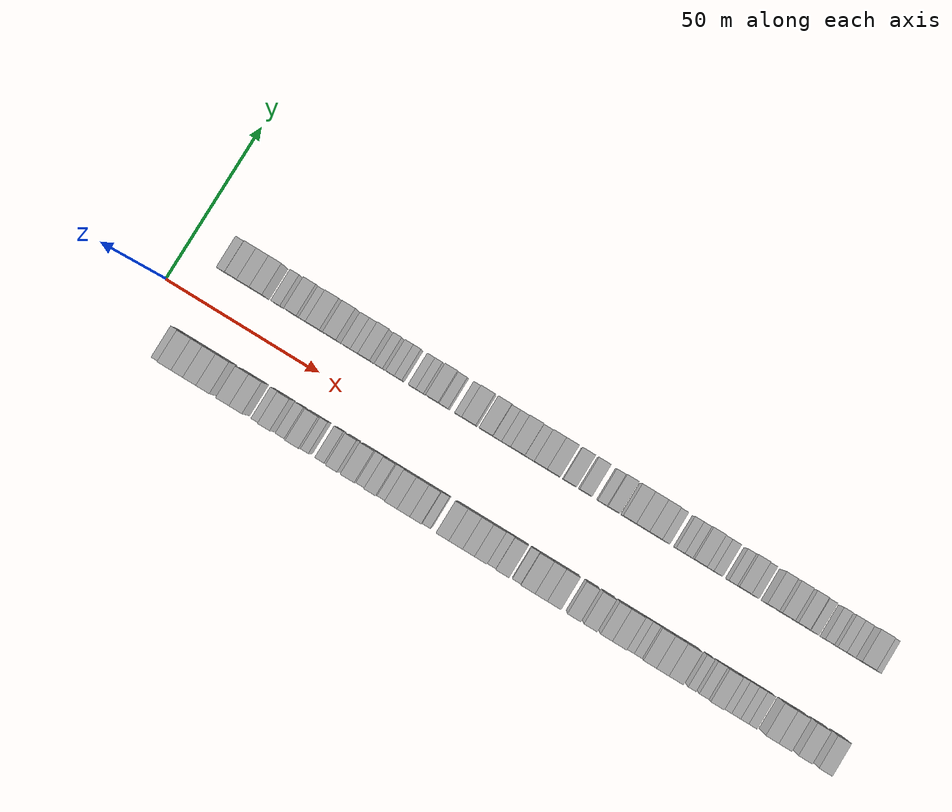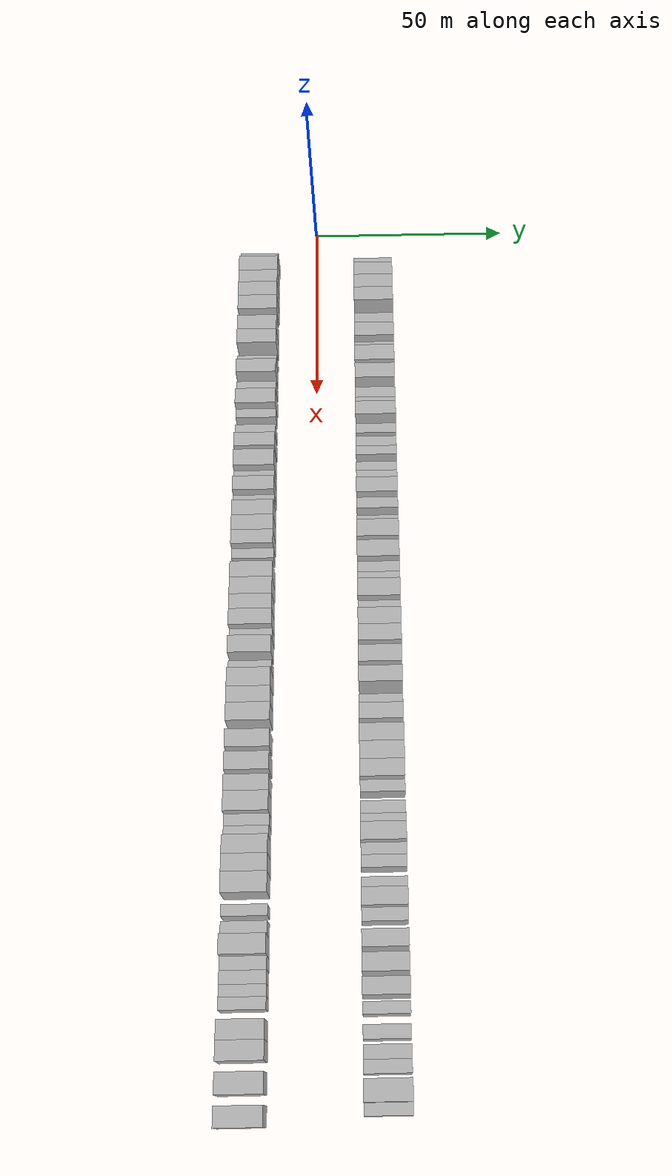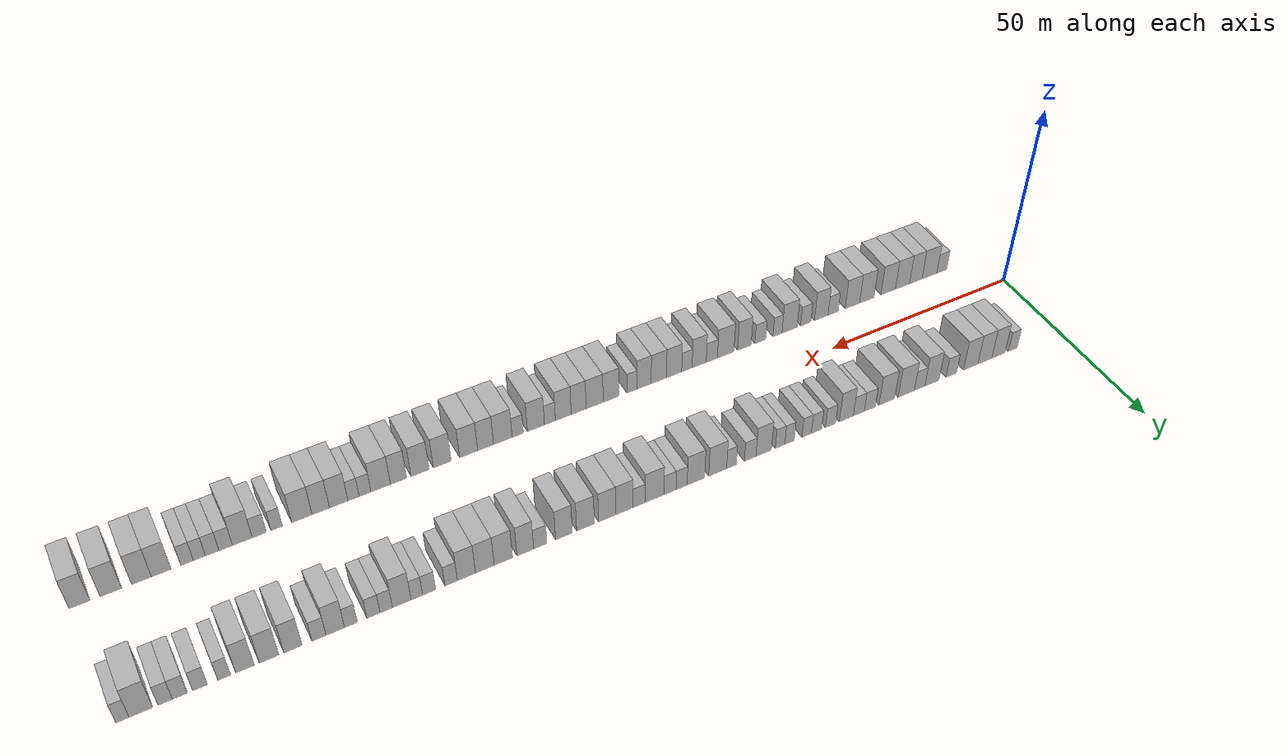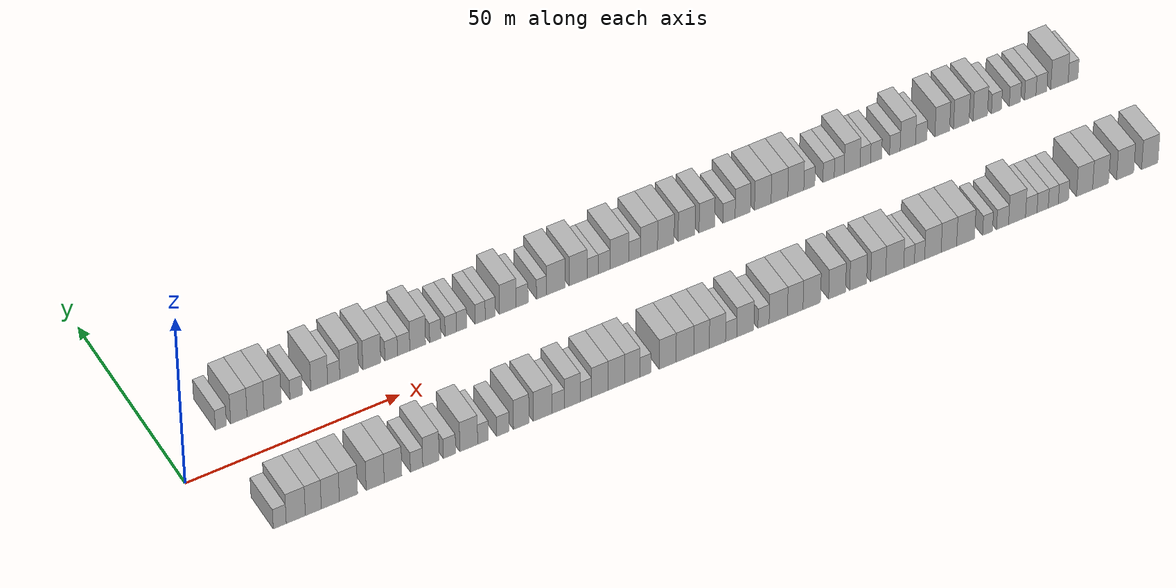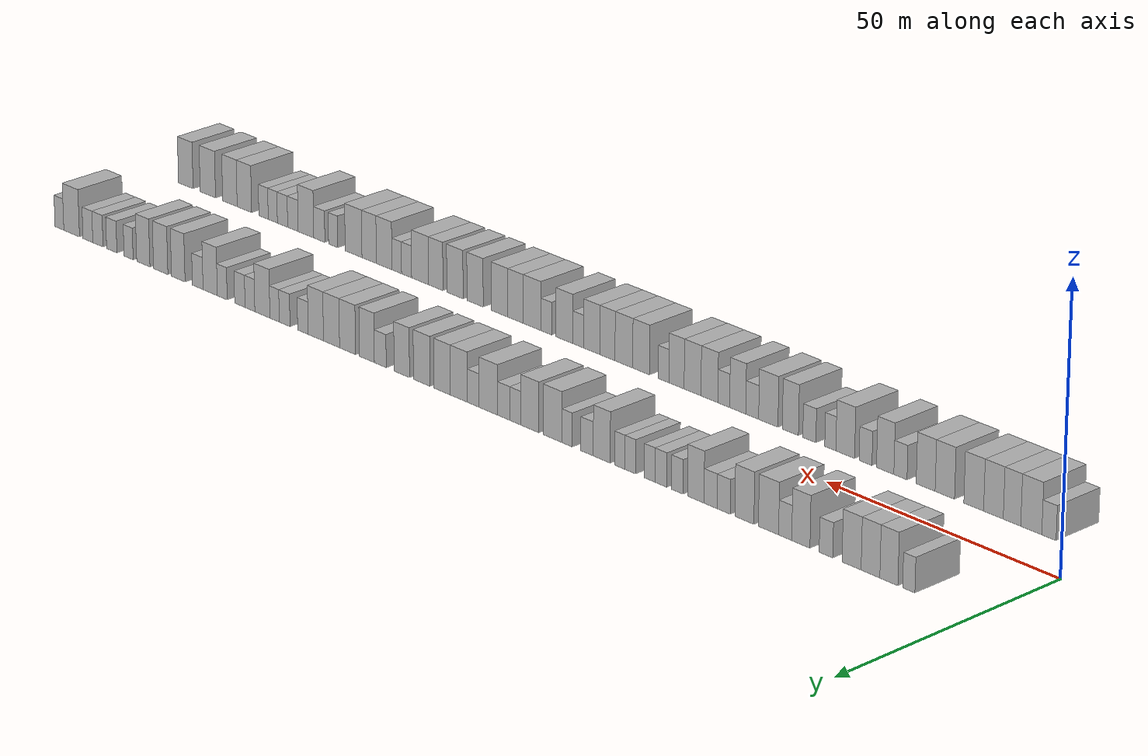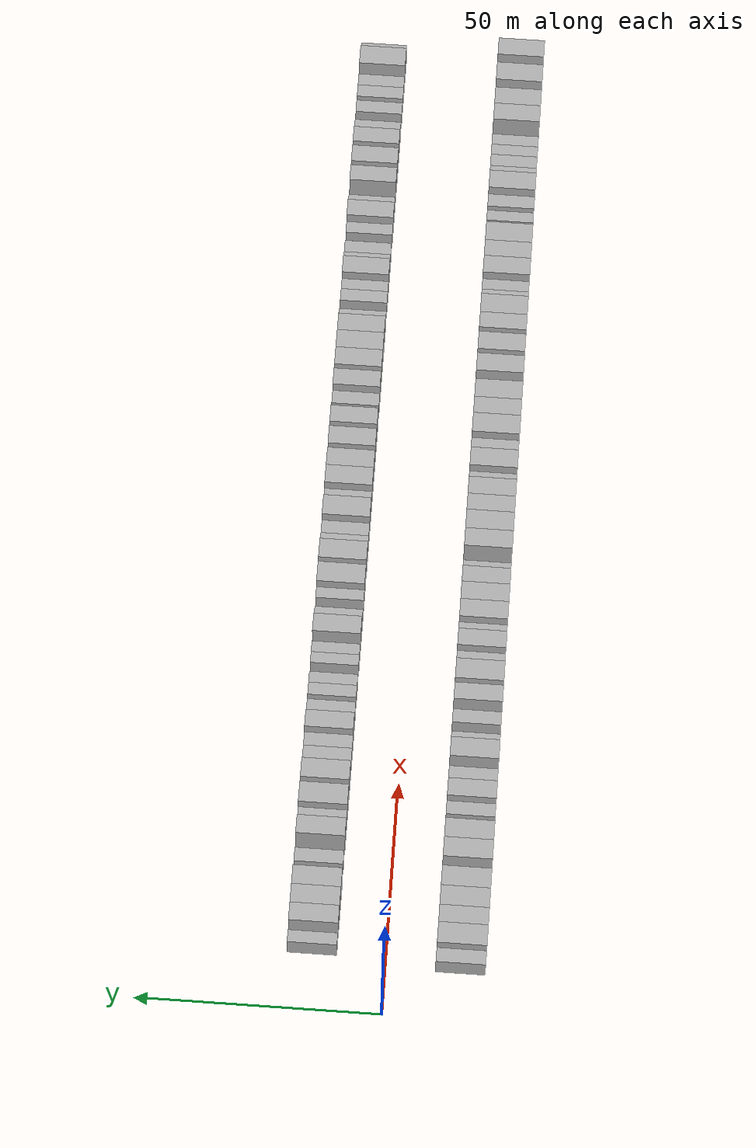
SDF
<sdf version="1.6">
 <world name="default">
  <scene>
   <sky><clouds><speed>12</speed></clouds></sky>
   <ambient>0.4 0.4 0.4 1</ambient>
   <background>0.7 0.7 0.7 1</background>
   <shadows>1</shadows>
  </scene>
  <gravity>0 0 -9.8066</gravity>
  <magnetic_field>6e-06 2.3e-05 -4.2e-05</magnetic_field>
  <physics default="0" name="default_physics" type="ode">
   <ode>
    <solver>
     <type>quick</type>
     <iters>10</iters>
     <sor>1.0</sor>
     <use_dynamic_moi_rescaling>0</use_dynamic_moi_rescaling>
    </solver>
    <constraints>
     <cfm>0</cfm>
     <erp>0.2</erp>
     <contact_max_correcting_vel>100</contact_max_correcting_vel>
     <contact_surface_layer>0.001</contact_surface_layer>
    </constraints>
   </ode>
   <max_step_size>0.004</max_step_size>
   <real_time_factor>1</real_time_factor>
   <real_time_update_rate>250</real_time_update_rate>
  </physics>
  <light name="sun" type="directional">
   <pose>0 0 10 0 0 0</pose>
   <diffuse>0.8 0.8 0.8 1</diffuse>
   <specular>0.2 0.2 0.2 1</specular>
   <attenuation>
    <range>1000</range>
    <constant>0.9</constant>
    <linear>0.01</linear>
    <quadratic>0.001</quadratic>
   </attenuation>
   <direction>-0.5 0.1 -0.9</direction>
  </light>
  <model name="building_1">
   <static>1</static>
   <pose>13.2862 15.0000 0 0.000000 0.000000 1.570796</pose>
   <link name="link">
    <pose>0 0 3.00 0 0 0</pose>
    <collision name="collision"><geometry><box><size>10.0000 2.5724 6.0000</size></box></geometry></collision>
    <visual name="visual">
     <cast_shadows>0</cast_shadows>
     <geometry><box><size>10.0000 2.5724 6.0000</size></box></geometry>
     <material>
      <script>
       <uri>model://HANNAS_wall/materials/scripts</uri>
       <uri>model://HANNAS_wall/materials/textures</uri>
       <name>vrc/HANNAS_wall</name>
      </script>
     </material>
    </visual>
   </link>
  </model>
  <model name="building_2">
   <static>1</static>
   <pose>17.4752 15.0000 0 0.000000 0.000000 1.570796</pose>
   <link name="link">
    <pose>0 0 4.50 0 0 0</pose>
    <collision name="collision"><geometry><box><size>10.0000 3.8055 9.0000</size></box></geometry></collision>
    <visual name="visual">
     <cast_shadows>0</cast_shadows>
     <geometry><box><size>10.0000 3.8055 9.0000</size></box></geometry>
     <material>
      <script>
       <uri>model://HANNAS_wall/materials/scripts</uri>
       <uri>model://HANNAS_wall/materials/textures</uri>
       <name>vrc/HANNAS_wall</name>
      </script>
     </material>
    </visual>
   </link>
  </model>
  <model name="building_3">
   <static>1</static>
   <pose>21.3710 15.0000 0 0.000000 0.000000 1.570796</pose>
   <link name="link">
    <pose>0 0 4.50 0 0 0</pose>
    <collision name="collision"><geometry><box><size>10.0000 3.9862 9.0000</size></box></geometry></collision>
    <visual name="visual">
     <cast_shadows>0</cast_shadows>
     <geometry><box><size>10.0000 3.9862 9.0000</size></box></geometry>
     <material>
      <script>
       <uri>model://HANNAS_wall/materials/scripts</uri>
       <uri>model://HANNAS_wall/materials/textures</uri>
       <name>vrc/HANNAS_wall</name>
      </script>
     </material>
    </visual>
   </link>
  </model>
  <model name="building_4">
   <static>1</static>
   <pose>25.3962 15.0000 0 0.000000 0.000000 1.570796</pose>
   <link name="link">
    <pose>0 0 4.50 0 0 0</pose>
    <collision name="collision"><geometry><box><size>10.0000 4.0641 9.0000</size></box></geometry></collision>
    <visual name="visual">
     <cast_shadows>0</cast_shadows>
     <geometry><box><size>10.0000 4.0641 9.0000</size></box></geometry>
     <material>
      <script>
       <uri>model://HANNAS_wall/materials/scripts</uri>
       <uri>model://HANNAS_wall/materials/textures</uri>
       <name>vrc/HANNAS_wall</name>
      </script>
     </material>
    </visual>
   </link>
  </model>
  <model name="building_5">
   <static>1</static>
   <pose>30.8911 15.0000 0 0.000000 0.000000 1.570796</pose>
   <link name="link">
    <pose>0 0 3.00 0 0 0</pose>
    <collision name="collision"><geometry><box><size>10.0000 2.9257 6.0000</size></box></geometry></collision>
    <visual name="visual">
     <cast_shadows>0</cast_shadows>
     <geometry><box><size>10.0000 2.9257 6.0000</size></box></geometry>
     <material>
      <script>
       <uri>model://HANNAS_wall/materials/scripts</uri>
       <uri>model://HANNAS_wall/materials/textures</uri>
       <name>vrc/HANNAS_wall</name>
      </script>
     </material>
    </visual>
   </link>
  </model>
  <model name="building_6">
   <static>1</static>
   <pose>36.3340 15.0000 0 0.000000 0.000000 1.570796</pose>
   <link name="link">
    <pose>0 0 4.50 0 0 0</pose>
    <collision name="collision"><geometry><box><size>10.0000 3.9601 9.0000</size></box></geometry></collision>
    <visual name="visual">
     <cast_shadows>0</cast_shadows>
     <geometry><box><size>10.0000 3.9601 9.0000</size></box></geometry>
     <material>
      <script>
       <uri>model://HANNAS_wall/materials/scripts</uri>
       <uri>model://HANNAS_wall/materials/textures</uri>
       <name>vrc/HANNAS_wall</name>
      </script>
     </material>
    </visual>
   </link>
  </model>
  <model name="building_7">
   <static>1</static>
   <pose>39.7516 15.0000 0 0.000000 0.000000 1.570796</pose>
   <link name="link">
    <pose>0 0 3.00 0 0 0</pose>
    <collision name="collision"><geometry><box><size>10.0000 2.8751 6.0000</size></box></geometry></collision>
    <visual name="visual">
     <cast_shadows>0</cast_shadows>
     <geometry><box><size>10.0000 2.8751 6.0000</size></box></geometry>
     <material>
      <script>
       <uri>model://HANNAS_wall/materials/scripts</uri>
       <uri>model://HANNAS_wall/materials/textures</uri>
       <name>vrc/HANNAS_wall</name>
      </script>
     </material>
    </visual>
   </link>
  </model>
  <model name="building_8">
   <static>1</static>
   <pose>43.4057 15.0000 0 0.000000 0.000000 1.570796</pose>
   <link name="link">
    <pose>0 0 4.50 0 0 0</pose>
    <collision name="collision"><geometry><box><size>10.0000 4.4330 9.0000</size></box></geometry></collision>
    <visual name="visual">
     <cast_shadows>0</cast_shadows>
     <geometry><box><size>10.0000 4.4330 9.0000</size></box></geometry>
     <material>
      <script>
       <uri>model://HANNAS_wall/materials/scripts</uri>
       <uri>model://HANNAS_wall/materials/textures</uri>
       <name>vrc/HANNAS_wall</name>
      </script>
     </material>
    </visual>
   </link>
  </model>
  <model name="building_9">
   <static>1</static>
   <pose>48.7348 15.0000 0 0.000000 0.000000 1.570796</pose>
   <link name="link">
    <pose>0 0 4.50 0 0 0</pose>
    <collision name="collision"><geometry><box><size>10.0000 4.2253 9.0000</size></box></geometry></collision>
    <visual name="visual">
     <cast_shadows>0</cast_shadows>
     <geometry><box><size>10.0000 4.2253 9.0000</size></box></geometry>
     <material>
      <script>
       <uri>model://HANNAS_wall/materials/scripts</uri>
       <uri>model://HANNAS_wall/materials/textures</uri>
       <name>vrc/HANNAS_wall</name>
      </script>
     </material>
    </visual>
   </link>
  </model>
  <model name="building_10">
   <static>1</static>
   <pose>53.3366 15.0000 0 0.000000 0.000000 1.570796</pose>
   <link name="link">
    <pose>0 0 3.00 0 0 0</pose>
    <collision name="collision"><geometry><box><size>10.0000 2.9783 6.0000</size></box></geometry></collision>
    <visual name="visual">
     <cast_shadows>0</cast_shadows>
     <geometry><box><size>10.0000 2.9783 6.0000</size></box></geometry>
     <material>
      <script>
       <uri>model://HANNAS_wall/materials/scripts</uri>
       <uri>model://HANNAS_wall/materials/textures</uri>
       <name>vrc/HANNAS_wall</name>
      </script>
     </material>
    </visual>
   </link>
  </model>
  <model name="building_11">
   <static>1</static>
   <pose>56.2876 15.0000 0 0.000000 0.000000 1.570796</pose>
   <link name="link">
    <pose>0 0 3.00 0 0 0</pose>
    <collision name="collision"><geometry><box><size>10.0000 2.9236 6.0000</size></box></geometry></collision>
    <visual name="visual">
     <cast_shadows>0</cast_shadows>
     <geometry><box><size>10.0000 2.9236 6.0000</size></box></geometry>
     <material>
      <script>
       <uri>model://HANNAS_wall/materials/scripts</uri>
       <uri>model://HANNAS_wall/materials/textures</uri>
       <name>vrc/HANNAS_wall</name>
      </script>
     </material>
    </visual>
   </link>
  </model>
  <model name="building_12">
   <static>1</static>
   <pose>59.6168 15.0000 0 0.000000 0.000000 1.570796</pose>
   <link name="link">
    <pose>0 0 4.50 0 0 0</pose>
    <collision name="collision"><geometry><box><size>10.0000 3.7350 9.0000</size></box></geometry></collision>
    <visual name="visual">
     <cast_shadows>0</cast_shadows>
     <geometry><box><size>10.0000 3.7350 9.0000</size></box></geometry>
     <material>
      <script>
       <uri>model://HANNAS_wall/materials/scripts</uri>
       <uri>model://HANNAS_wall/materials/textures</uri>
       <name>vrc/HANNAS_wall</name>
      </script>
     </material>
    </visual>
   </link>
  </model>
  <model name="building_13">
   <static>1</static>
   <pose>63.8142 15.0000 0 0.000000 0.000000 1.570796</pose>
   <link name="link">
    <pose>0 0 3.00 0 0 0</pose>
    <collision name="collision"><geometry><box><size>10.0000 2.6598 6.0000</size></box></geometry></collision>
    <visual name="visual">
     <cast_shadows>0</cast_shadows>
     <geometry><box><size>10.0000 2.6598 6.0000</size></box></geometry>
     <material>
      <script>
       <uri>model://HANNAS_wall/materials/scripts</uri>
       <uri>model://HANNAS_wall/materials/textures</uri>
       <name>vrc/HANNAS_wall</name>
      </script>
     </material>
    </visual>
   </link>
  </model>
  <model name="building_14">
   <static>1</static>
   <pose>67.4996 15.0000 0 0.000000 0.000000 1.570796</pose>
   <link name="link">
    <pose>0 0 3.00 0 0 0</pose>
    <collision name="collision"><geometry><box><size>10.0000 2.7109 6.0000</size></box></geometry></collision>
    <visual name="visual">
     <cast_shadows>0</cast_shadows>
     <geometry><box><size>10.0000 2.7109 6.0000</size></box></geometry>
     <material>
      <script>
       <uri>model://HANNAS_wall/materials/scripts</uri>
       <uri>model://HANNAS_wall/materials/textures</uri>
       <name>vrc/HANNAS_wall</name>
      </script>
     </material>
    </visual>
   </link>
  </model>
  <model name="building_15">
   <static>1</static>
   <pose>70.0767 15.0000 0 0.000000 0.000000 1.570796</pose>
   <link name="link">
    <pose>0 0 3.00 0 0 0</pose>
    <collision name="collision"><geometry><box><size>10.0000 2.4434 6.0000</size></box></geometry></collision>
    <visual name="visual">
     <cast_shadows>0</cast_shadows>
     <geometry><box><size>10.0000 2.4434 6.0000</size></box></geometry>
     <material>
      <script>
       <uri>model://HANNAS_wall/materials/scripts</uri>
       <uri>model://HANNAS_wall/materials/textures</uri>
       <name>vrc/HANNAS_wall</name>
      </script>
     </material>
    </visual>
   </link>
  </model>
  <model name="building_16">
   <static>1</static>
   <pose>74.5183 15.0000 0 0.000000 0.000000 1.570796</pose>
   <link name="link">
    <pose>0 0 3.00 0 0 0</pose>
    <collision name="collision"><geometry><box><size>10.0000 2.4397 6.0000</size></box></geometry></collision>
    <visual name="visual">
     <cast_shadows>0</cast_shadows>
     <geometry><box><size>10.0000 2.4397 6.0000</size></box></geometry>
     <material>
      <script>
       <uri>model://HANNAS_wall/materials/scripts</uri>
       <uri>model://HANNAS_wall/materials/textures</uri>
       <name>vrc/HANNAS_wall</name>
      </script>
     </material>
    </visual>
   </link>
  </model>
  <model name="building_17">
   <static>1</static>
   <pose>76.9490 15.0000 0 0.000000 0.000000 1.570796</pose>
   <link name="link">
    <pose>0 0 3.00 0 0 0</pose>
    <collision name="collision"><geometry><box><size>10.0000 2.4216 6.0000</size></box></geometry></collision>
    <visual name="visual">
     <cast_shadows>0</cast_shadows>
     <geometry><box><size>10.0000 2.4216 6.0000</size></box></geometry>
     <material>
      <script>
       <uri>model://HANNAS_wall/materials/scripts</uri>
       <uri>model://HANNAS_wall/materials/textures</uri>
       <name>vrc/HANNAS_wall</name>
      </script>
     </material>
    </visual>
   </link>
  </model>
  <model name="building_18">
   <static>1</static>
   <pose>81.1411 15.0000 0 0.000000 0.000000 1.570796</pose>
   <link name="link">
    <pose>0 0 4.50 0 0 0</pose>
    <collision name="collision"><geometry><box><size>10.0000 3.9626 9.0000</size></box></geometry></collision>
    <visual name="visual">
     <cast_shadows>0</cast_shadows>
     <geometry><box><size>10.0000 3.9626 9.0000</size></box></geometry>
     <material>
      <script>
       <uri>model://HANNAS_wall/materials/scripts</uri>
       <uri>model://HANNAS_wall/materials/textures</uri>
       <name>vrc/HANNAS_wall</name>
      </script>
     </material>
    </visual>
   </link>
  </model>
  <model name="building_19">
   <static>1</static>
   <pose>84.5773 15.0000 0 0.000000 0.000000 1.570796</pose>
   <link name="link">
    <pose>0 0 3.00 0 0 0</pose>
    <collision name="collision"><geometry><box><size>10.0000 2.9098 6.0000</size></box></geometry></collision>
    <visual name="visual">
     <cast_shadows>0</cast_shadows>
     <geometry><box><size>10.0000 2.9098 6.0000</size></box></geometry>
     <material>
      <script>
       <uri>model://HANNAS_wall/materials/scripts</uri>
       <uri>model://HANNAS_wall/materials/textures</uri>
       <name>vrc/HANNAS_wall</name>
      </script>
     </material>
    </visual>
   </link>
  </model>
  <model name="building_20">
   <static>1</static>
   <pose>89.2566 15.0000 0 0.000000 0.000000 1.570796</pose>
   <link name="link">
    <pose>0 0 3.00 0 0 0</pose>
    <collision name="collision"><geometry><box><size>10.0000 2.4487 6.0000</size></box></geometry></collision>
    <visual name="visual">
     <cast_shadows>0</cast_shadows>
     <geometry><box><size>10.0000 2.4487 6.0000</size></box></geometry>
     <material>
      <script>
       <uri>model://HANNAS_wall/materials/scripts</uri>
       <uri>model://HANNAS_wall/materials/textures</uri>
       <name>vrc/HANNAS_wall</name>
      </script>
     </material>
    </visual>
   </link>
  </model>
  <model name="building_21">
   <static>1</static>
   <pose>92.7052 15.0000 0 0.000000 0.000000 1.570796</pose>
   <link name="link">
    <pose>0 0 4.50 0 0 0</pose>
    <collision name="collision"><geometry><box><size>10.0000 4.4486 9.0000</size></box></geometry></collision>
    <visual name="visual">
     <cast_shadows>0</cast_shadows>
     <geometry><box><size>10.0000 4.4486 9.0000</size></box></geometry>
     <material>
      <script>
       <uri>model://HANNAS_wall/materials/scripts</uri>
       <uri>model://HANNAS_wall/materials/textures</uri>
       <name>vrc/HANNAS_wall</name>
      </script>
     </material>
    </visual>
   </link>
  </model>
  <model name="building_22">
   <static>1</static>
   <pose>98.0822 15.0000 0 0.000000 0.000000 1.570796</pose>
   <link name="link">
    <pose>0 0 4.50 0 0 0</pose>
    <collision name="collision"><geometry><box><size>10.0000 4.3055 9.0000</size></box></geometry></collision>
    <visual name="visual">
     <cast_shadows>0</cast_shadows>
     <geometry><box><size>10.0000 4.3055 9.0000</size></box></geometry>
     <material>
      <script>
       <uri>model://HANNAS_wall/materials/scripts</uri>
       <uri>model://HANNAS_wall/materials/textures</uri>
       <name>vrc/HANNAS_wall</name>
      </script>
     </material>
    </visual>
   </link>
  </model>
  <model name="building_23">
   <static>1</static>
   <pose>101.5895 15.0000 0 0.000000 0.000000 1.570796</pose>
   <link name="link">
    <pose>0 0 3.00 0 0 0</pose>
    <collision name="collision"><geometry><box><size>10.0000 2.7089 6.0000</size></box></geometry></collision>
    <visual name="visual">
     <cast_shadows>0</cast_shadows>
     <geometry><box><size>10.0000 2.7089 6.0000</size></box></geometry>
     <material>
      <script>
       <uri>model://HANNAS_wall/materials/scripts</uri>
       <uri>model://HANNAS_wall/materials/textures</uri>
       <name>vrc/HANNAS_wall</name>
      </script>
     </material>
    </visual>
   </link>
  </model>
  <model name="building_24">
   <static>1</static>
   <pose>104.3950 15.0000 0 0.000000 0.000000 1.570796</pose>
   <link name="link">
    <pose>0 0 3.00 0 0 0</pose>
    <collision name="collision"><geometry><box><size>10.0000 2.9022 6.0000</size></box></geometry></collision>
    <visual name="visual">
     <cast_shadows>0</cast_shadows>
     <geometry><box><size>10.0000 2.9022 6.0000</size></box></geometry>
     <material>
      <script>
       <uri>model://HANNAS_wall/materials/scripts</uri>
       <uri>model://HANNAS_wall/materials/textures</uri>
       <name>vrc/HANNAS_wall</name>
      </script>
     </material>
    </visual>
   </link>
  </model>
  <model name="building_25">
   <static>1</static>
   <pose>108.0881 15.0000 0 0.000000 0.000000 1.570796</pose>
   <link name="link">
    <pose>0 0 4.50 0 0 0</pose>
    <collision name="collision"><geometry><box><size>10.0000 4.4841 9.0000</size></box></geometry></collision>
    <visual name="visual">
     <cast_shadows>0</cast_shadows>
     <geometry><box><size>10.0000 4.4841 9.0000</size></box></geometry>
     <material>
      <script>
       <uri>model://HANNAS_wall/materials/scripts</uri>
       <uri>model://HANNAS_wall/materials/textures</uri>
       <name>vrc/HANNAS_wall</name>
      </script>
     </material>
    </visual>
   </link>
  </model>
  <model name="building_26">
   <static>1</static>
   <pose>111.7850 15.0000 0 0.000000 0.000000 1.570796</pose>
   <link name="link">
    <pose>0 0 3.00 0 0 0</pose>
    <collision name="collision"><geometry><box><size>10.0000 2.9097 6.0000</size></box></geometry></collision>
    <visual name="visual">
     <cast_shadows>0</cast_shadows>
     <geometry><box><size>10.0000 2.9097 6.0000</size></box></geometry>
     <material>
      <script>
       <uri>model://HANNAS_wall/materials/scripts</uri>
       <uri>model://HANNAS_wall/materials/textures</uri>
       <name>vrc/HANNAS_wall</name>
      </script>
     </material>
    </visual>
   </link>
  </model>
  <model name="building_27">
   <static>1</static>
   <pose>115.3012 15.0000 0 0.000000 0.000000 1.570796</pose>
   <link name="link">
    <pose>0 0 4.50 0 0 0</pose>
    <collision name="collision"><geometry><box><size>10.0000 4.1226 9.0000</size></box></geometry></collision>
    <visual name="visual">
     <cast_shadows>0</cast_shadows>
     <geometry><box><size>10.0000 4.1226 9.0000</size></box></geometry>
     <material>
      <script>
       <uri>model://HANNAS_wall/materials/scripts</uri>
       <uri>model://HANNAS_wall/materials/textures</uri>
       <name>vrc/HANNAS_wall</name>
      </script>
     </material>
    </visual>
   </link>
  </model>
  <model name="building_28">
   <static>1</static>
   <pose>119.3822 15.0000 0 0.000000 0.000000 1.570796</pose>
   <link name="link">
    <pose>0 0 4.50 0 0 0</pose>
    <collision name="collision"><geometry><box><size>10.0000 4.0395 9.0000</size></box></geometry></collision>
    <visual name="visual">
     <cast_shadows>0</cast_shadows>
     <geometry><box><size>10.0000 4.0395 9.0000</size></box></geometry>
     <material>
      <script>
       <uri>model://HANNAS_wall/materials/scripts</uri>
       <uri>model://HANNAS_wall/materials/textures</uri>
       <name>vrc/HANNAS_wall</name>
      </script>
     </material>
    </visual>
   </link>
  </model>
  <model name="building_29">
   <static>1</static>
   <pose>124.4516 15.0000 0 0.000000 0.000000 1.570796</pose>
   <link name="link">
    <pose>0 0 4.50 0 0 0</pose>
    <collision name="collision"><geometry><box><size>10.0000 4.0994 9.0000</size></box></geometry></collision>
    <visual name="visual">
     <cast_shadows>0</cast_shadows>
     <geometry><box><size>10.0000 4.0994 9.0000</size></box></geometry>
     <material>
      <script>
       <uri>model://HANNAS_wall/materials/scripts</uri>
       <uri>model://HANNAS_wall/materials/textures</uri>
       <name>vrc/HANNAS_wall</name>
      </script>
     </material>
    </visual>
   </link>
  </model>
  <model name="building_30">
   <static>1</static>
   <pose>129.4214 15.0000 0 0.000000 0.000000 1.570796</pose>
   <link name="link">
    <pose>0 0 4.50 0 0 0</pose>
    <collision name="collision"><geometry><box><size>10.0000 3.8402 9.0000</size></box></geometry></collision>
    <visual name="visual">
     <cast_shadows>0</cast_shadows>
     <geometry><box><size>10.0000 3.8402 9.0000</size></box></geometry>
     <material>
      <script>
       <uri>model://HANNAS_wall/materials/scripts</uri>
       <uri>model://HANNAS_wall/materials/textures</uri>
       <name>vrc/HANNAS_wall</name>
      </script>
     </material>
    </visual>
   </link>
  </model>
  <model name="building_31">
   <static>1</static>
   <pose>134.8365 15.0000 0 0.000000 0.000000 1.570796</pose>
   <link name="link">
    <pose>0 0 3.00 0 0 0</pose>
    <collision name="collision"><geometry><box><size>10.0000 2.9901 6.0000</size></box></geometry></collision>
    <visual name="visual">
     <cast_shadows>0</cast_shadows>
     <geometry><box><size>10.0000 2.9901 6.0000</size></box></geometry>
     <material>
      <script>
       <uri>model://HANNAS_wall/materials/scripts</uri>
       <uri>model://HANNAS_wall/materials/textures</uri>
       <name>vrc/HANNAS_wall</name>
      </script>
     </material>
    </visual>
   </link>
  </model>
  <model name="building_32">
   <static>1</static>
   <pose>138.2175 15.0000 0 0.000000 0.000000 1.570796</pose>
   <link name="link">
    <pose>0 0 4.50 0 0 0</pose>
    <collision name="collision"><geometry><box><size>10.0000 3.7719 9.0000</size></box></geometry></collision>
    <visual name="visual">
     <cast_shadows>0</cast_shadows>
     <geometry><box><size>10.0000 3.7719 9.0000</size></box></geometry>
     <material>
      <script>
       <uri>model://HANNAS_wall/materials/scripts</uri>
       <uri>model://HANNAS_wall/materials/textures</uri>
       <name>vrc/HANNAS_wall</name>
      </script>
     </material>
    </visual>
   </link>
  </model>
  <model name="building_33">
   <static>1</static>
   <pose>143.1482 15.0000 0 0.000000 0.000000 1.570796</pose>
   <link name="link">
    <pose>0 0 4.50 0 0 0</pose>
    <collision name="collision"><geometry><box><size>10.0000 4.0895 9.0000</size></box></geometry></collision>
    <visual name="visual">
     <cast_shadows>0</cast_shadows>
     <geometry><box><size>10.0000 4.0895 9.0000</size></box></geometry>
     <material>
      <script>
       <uri>model://HANNAS_wall/materials/scripts</uri>
       <uri>model://HANNAS_wall/materials/textures</uri>
       <name>vrc/HANNAS_wall</name>
      </script>
     </material>
    </visual>
   </link>
  </model>
  <model name="building_34">
   <static>1</static>
   <pose>147.2556 15.0000 0 0.000000 0.000000 1.570796</pose>
   <link name="link">
    <pose>0 0 4.50 0 0 0</pose>
    <collision name="collision"><geometry><box><size>10.0000 4.1252 9.0000</size></box></geometry></collision>
    <visual name="visual">
     <cast_shadows>0</cast_shadows>
     <geometry><box><size>10.0000 4.1252 9.0000</size></box></geometry>
     <material>
      <script>
       <uri>model://HANNAS_wall/materials/scripts</uri>
       <uri>model://HANNAS_wall/materials/textures</uri>
       <name>vrc/HANNAS_wall</name>
      </script>
     </material>
    </visual>
   </link>
  </model>
  <model name="building_35">
   <static>1</static>
   <pose>151.2956 15.0000 0 0.000000 0.000000 1.570796</pose>
   <link name="link">
    <pose>0 0 4.50 0 0 0</pose>
    <collision name="collision"><geometry><box><size>10.0000 3.9548 9.0000</size></box></geometry></collision>
    <visual name="visual">
     <cast_shadows>0</cast_shadows>
     <geometry><box><size>10.0000 3.9548 9.0000</size></box></geometry>
     <material>
      <script>
       <uri>model://HANNAS_wall/materials/scripts</uri>
       <uri>model://HANNAS_wall/materials/textures</uri>
       <name>vrc/HANNAS_wall</name>
      </script>
     </material>
    </visual>
   </link>
  </model>
  <model name="building_36">
   <static>1</static>
   <pose>154.6378 15.0000 0 0.000000 0.000000 1.570796</pose>
   <link name="link">
    <pose>0 0 3.00 0 0 0</pose>
    <collision name="collision"><geometry><box><size>10.0000 2.7296 6.0000</size></box></geometry></collision>
    <visual name="visual">
     <cast_shadows>0</cast_shadows>
     <geometry><box><size>10.0000 2.7296 6.0000</size></box></geometry>
     <material>
      <script>
       <uri>model://HANNAS_wall/materials/scripts</uri>
       <uri>model://HANNAS_wall/materials/textures</uri>
       <name>vrc/HANNAS_wall</name>
      </script>
     </material>
    </visual>
   </link>
  </model>
  <model name="building_37">
   <static>1</static>
   <pose>159.4041 15.0000 0 0.000000 0.000000 1.570796</pose>
   <link name="link">
    <pose>0 0 3.00 0 0 0</pose>
    <collision name="collision"><geometry><box><size>10.0000 2.8030 6.0000</size></box></geometry></collision>
    <visual name="visual">
     <cast_shadows>0</cast_shadows>
     <geometry><box><size>10.0000 2.8030 6.0000</size></box></geometry>
     <material>
      <script>
       <uri>model://HANNAS_wall/materials/scripts</uri>
       <uri>model://HANNAS_wall/materials/textures</uri>
       <name>vrc/HANNAS_wall</name>
      </script>
     </material>
    </visual>
   </link>
  </model>
  <model name="building_38">
   <static>1</static>
   <pose>162.0353 15.0000 0 0.000000 0.000000 1.570796</pose>
   <link name="link">
    <pose>0 0 3.00 0 0 0</pose>
    <collision name="collision"><geometry><box><size>10.0000 2.4594 6.0000</size></box></geometry></collision>
    <visual name="visual">
     <cast_shadows>0</cast_shadows>
     <geometry><box><size>10.0000 2.4594 6.0000</size></box></geometry>
     <material>
      <script>
       <uri>model://HANNAS_wall/materials/scripts</uri>
       <uri>model://HANNAS_wall/materials/textures</uri>
       <name>vrc/HANNAS_wall</name>
      </script>
     </material>
    </visual>
   </link>
  </model>
  <model name="building_39">
   <static>1</static>
   <pose>165.2494 15.0000 0 0.000000 0.000000 1.570796</pose>
   <link name="link">
    <pose>0 0 4.50 0 0 0</pose>
    <collision name="collision"><geometry><box><size>10.0000 3.9687 9.0000</size></box></geometry></collision>
    <visual name="visual">
     <cast_shadows>0</cast_shadows>
     <geometry><box><size>10.0000 3.9687 9.0000</size></box></geometry>
     <material>
      <script>
       <uri>model://HANNAS_wall/materials/scripts</uri>
       <uri>model://HANNAS_wall/materials/textures</uri>
       <name>vrc/HANNAS_wall</name>
      </script>
     </material>
    </visual>
   </link>
  </model>
  <model name="building_40">
   <static>1</static>
   <pose>168.5299 15.0000 0 0.000000 0.000000 1.570796</pose>
   <link name="link">
    <pose>0 0 3.00 0 0 0</pose>
    <collision name="collision"><geometry><box><size>10.0000 2.5924 6.0000</size></box></geometry></collision>
    <visual name="visual">
     <cast_shadows>0</cast_shadows>
     <geometry><box><size>10.0000 2.5924 6.0000</size></box></geometry>
     <material>
      <script>
       <uri>model://HANNAS_wall/materials/scripts</uri>
       <uri>model://HANNAS_wall/materials/textures</uri>
       <name>vrc/HANNAS_wall</name>
      </script>
     </material>
    </visual>
   </link>
  </model>
  <model name="building_41">
   <static>1</static>
   <pose>171.2062 15.0000 0 0.000000 0.000000 1.570796</pose>
   <link name="link">
    <pose>0 0 3.00 0 0 0</pose>
    <collision name="collision"><geometry><box><size>10.0000 2.7601 6.0000</size></box></geometry></collision>
    <visual name="visual">
     <cast_shadows>0</cast_shadows>
     <geometry><box><size>10.0000 2.7601 6.0000</size></box></geometry>
     <material>
      <script>
       <uri>model://HANNAS_wall/materials/scripts</uri>
       <uri>model://HANNAS_wall/materials/textures</uri>
       <name>vrc/HANNAS_wall</name>
      </script>
     </material>
    </visual>
   </link>
  </model>
  <model name="building_42">
   <static>1</static>
   <pose>175.9025 15.0000 0 0.000000 0.000000 1.570796</pose>
   <link name="link">
    <pose>0 0 3.00 0 0 0</pose>
    <collision name="collision"><geometry><box><size>10.0000 2.6325 6.0000</size></box></geometry></collision>
    <visual name="visual">
     <cast_shadows>0</cast_shadows>
     <geometry><box><size>10.0000 2.6325 6.0000</size></box></geometry>
     <material>
      <script>
       <uri>model://HANNAS_wall/materials/scripts</uri>
       <uri>model://HANNAS_wall/materials/textures</uri>
       <name>vrc/HANNAS_wall</name>
      </script>
     </material>
    </visual>
   </link>
  </model>
  <model name="building_43">
   <static>1</static>
   <pose>179.1358 15.0000 0 0.000000 0.000000 1.570796</pose>
   <link name="link">
    <pose>0 0 4.50 0 0 0</pose>
    <collision name="collision"><geometry><box><size>10.0000 3.8341 9.0000</size></box></geometry></collision>
    <visual name="visual">
     <cast_shadows>0</cast_shadows>
     <geometry><box><size>10.0000 3.8341 9.0000</size></box></geometry>
     <material>
      <script>
       <uri>model://HANNAS_wall/materials/scripts</uri>
       <uri>model://HANNAS_wall/materials/textures</uri>
       <name>vrc/HANNAS_wall</name>
      </script>
     </material>
    </visual>
   </link>
  </model>
  <model name="building_44">
   <static>1</static>
   <pose>182.4893 15.0000 0 0.000000 0.000000 1.570796</pose>
   <link name="link">
    <pose>0 0 3.00 0 0 0</pose>
    <collision name="collision"><geometry><box><size>10.0000 2.8729 6.0000</size></box></geometry></collision>
    <visual name="visual">
     <cast_shadows>0</cast_shadows>
     <geometry><box><size>10.0000 2.8729 6.0000</size></box></geometry>
     <material>
      <script>
       <uri>model://HANNAS_wall/materials/scripts</uri>
       <uri>model://HANNAS_wall/materials/textures</uri>
       <name>vrc/HANNAS_wall</name>
      </script>
     </material>
    </visual>
   </link>
  </model>
  <model name="building_45">
   <static>1</static>
   <pose>187.7639 15.0000 0 0.000000 0.000000 1.570796</pose>
   <link name="link">
    <pose>0 0 4.50 0 0 0</pose>
    <collision name="collision"><geometry><box><size>10.0000 3.6764 9.0000</size></box></geometry></collision>
    <visual name="visual">
     <cast_shadows>0</cast_shadows>
     <geometry><box><size>10.0000 3.6764 9.0000</size></box></geometry>
     <material>
      <script>
       <uri>model://HANNAS_wall/materials/scripts</uri>
       <uri>model://HANNAS_wall/materials/textures</uri>
       <name>vrc/HANNAS_wall</name>
      </script>
     </material>
    </visual>
   </link>
  </model>
  <model name="building_46">
   <static>1</static>
   <pose>192.5586 15.0000 0 0.000000 0.000000 1.570796</pose>
   <link name="link">
    <pose>0 0 4.50 0 0 0</pose>
    <collision name="collision"><geometry><box><size>10.0000 3.9129 9.0000</size></box></geometry></collision>
    <visual name="visual">
     <cast_shadows>0</cast_shadows>
     <geometry><box><size>10.0000 3.9129 9.0000</size></box></geometry>
     <material>
      <script>
       <uri>model://HANNAS_wall/materials/scripts</uri>
       <uri>model://HANNAS_wall/materials/textures</uri>
       <name>vrc/HANNAS_wall</name>
      </script>
     </material>
    </visual>
   </link>
  </model>
  <model name="building_47">
   <static>1</static>
   <pose>197.3380 15.0000 0 0.000000 0.000000 1.570796</pose>
   <link name="link">
    <pose>0 0 4.50 0 0 0</pose>
    <collision name="collision"><geometry><box><size>10.0000 3.6460 9.0000</size></box></geometry></collision>
    <visual name="visual">
     <cast_shadows>0</cast_shadows>
     <geometry><box><size>10.0000 3.6460 9.0000</size></box></geometry>
     <material>
      <script>
       <uri>model://HANNAS_wall/materials/scripts</uri>
       <uri>model://HANNAS_wall/materials/textures</uri>
       <name>vrc/HANNAS_wall</name>
      </script>
     </material>
    </visual>
   </link>
  </model>
  <model name="building_48">
   <static>1</static>
   <pose>201.4136 15.0000 0 0.000000 0.000000 1.570796</pose>
   <link name="link">
    <pose>0 0 3.00 0 0 0</pose>
    <collision name="collision"><geometry><box><size>10.0000 2.5052 6.0000</size></box></geometry></collision>
    <visual name="visual">
     <cast_shadows>0</cast_shadows>
     <geometry><box><size>10.0000 2.5052 6.0000</size></box></geometry>
     <material>
      <script>
       <uri>model://HANNAS_wall/materials/scripts</uri>
       <uri>model://HANNAS_wall/materials/textures</uri>
       <name>vrc/HANNAS_wall</name>
      </script>
     </material>
    </visual>
   </link>
  </model>
  <model name="building_49">
   <static>1</static>
   <pose>206.1021 15.0000 0 0.000000 0.000000 1.570796</pose>
   <link name="link">
    <pose>0 0 3.00 0 0 0</pose>
    <collision name="collision"><geometry><box><size>10.0000 2.8717 6.0000</size></box></geometry></collision>
    <visual name="visual">
     <cast_shadows>0</cast_shadows>
     <geometry><box><size>10.0000 2.8717 6.0000</size></box></geometry>
     <material>
      <script>
       <uri>model://HANNAS_wall/materials/scripts</uri>
       <uri>model://HANNAS_wall/materials/textures</uri>
       <name>vrc/HANNAS_wall</name>
      </script>
     </material>
    </visual>
   </link>
  </model>
  <model name="building_50">
   <static>1</static>
   <pose>209.9766 15.0000 0 0.000000 0.000000 1.570796</pose>
   <link name="link">
    <pose>0 0 3.00 0 0 0</pose>
    <collision name="collision"><geometry><box><size>10.0000 2.8775 6.0000</size></box></geometry></collision>
    <visual name="visual">
     <cast_shadows>0</cast_shadows>
     <geometry><box><size>10.0000 2.8775 6.0000</size></box></geometry>
     <material>
      <script>
       <uri>model://HANNAS_wall/materials/scripts</uri>
       <uri>model://HANNAS_wall/materials/textures</uri>
       <name>vrc/HANNAS_wall</name>
      </script>
     </material>
    </visual>
   </link>
  </model>
  <model name="building_51">
   <static>1</static>
   <pose>212.7924 15.0000 0 0.000000 0.000000 1.570796</pose>
   <link name="link">
    <pose>0 0 3.00 0 0 0</pose>
    <collision name="collision"><geometry><box><size>10.0000 2.7541 6.0000</size></box></geometry></collision>
    <visual name="visual">
     <cast_shadows>0</cast_shadows>
     <geometry><box><size>10.0000 2.7541 6.0000</size></box></geometry>
     <material>
      <script>
       <uri>model://HANNAS_wall/materials/scripts</uri>
       <uri>model://HANNAS_wall/materials/textures</uri>
       <name>vrc/HANNAS_wall</name>
      </script>
     </material>
    </visual>
   </link>
  </model>
  <model name="building_52">
   <static>1</static>
   <pose>217.3848 15.0000 0 0.000000 0.000000 1.570796</pose>
   <link name="link">
    <pose>0 0 4.50 0 0 0</pose>
    <collision name="collision"><geometry><box><size>10.0000 4.4307 9.0000</size></box></geometry></collision>
    <visual name="visual">
     <cast_shadows>0</cast_shadows>
     <geometry><box><size>10.0000 4.4307 9.0000</size></box></geometry>
     <material>
      <script>
       <uri>model://HANNAS_wall/materials/scripts</uri>
       <uri>model://HANNAS_wall/materials/textures</uri>
       <name>vrc/HANNAS_wall</name>
      </script>
     </material>
    </visual>
   </link>
  </model>
  <model name="building_53">
   <static>1</static>
   <pose>220.8513 15.0000 0 0.000000 0.000000 1.570796</pose>
   <link name="link">
    <pose>0 0 3.00 0 0 0</pose>
    <collision name="collision"><geometry><box><size>10.0000 2.5022 6.0000</size></box></geometry></collision>
    <visual name="visual">
     <cast_shadows>0</cast_shadows>
     <geometry><box><size>10.0000 2.5022 6.0000</size></box></geometry>
     <material>
      <script>
       <uri>model://HANNAS_wall/materials/scripts</uri>
       <uri>model://HANNAS_wall/materials/textures</uri>
       <name>vrc/HANNAS_wall</name>
      </script>
     </material>
    </visual>
   </link>
  </model>
  <model name="building_54">
   <static>1</static>
   <pose>11.4987 -15.0000 0 0.000000 0.000000 1.570796</pose>
   <link name="link">
    <pose>0 0 3.00 0 0 0</pose>
    <collision name="collision"><geometry><box><size>10.0000 2.9974 6.0000</size></box></geometry></collision>
    <visual name="visual">
     <cast_shadows>0</cast_shadows>
     <geometry><box><size>10.0000 2.9974 6.0000</size></box></geometry>
     <material>
      <script>
       <uri>model://HANNAS_wall/materials/scripts</uri>
       <uri>model://HANNAS_wall/materials/textures</uri>
       <name>vrc/HANNAS_wall</name>
      </script>
     </material>
    </visual>
   </link>
  </model>
  <model name="building_55">
   <static>1</static>
   <pose>15.2125 -15.0000 0 0.000000 0.000000 1.570796</pose>
   <link name="link">
    <pose>0 0 4.50 0 0 0</pose>
    <collision name="collision"><geometry><box><size>10.0000 4.4302 9.0000</size></box></geometry></collision>
    <visual name="visual">
     <cast_shadows>0</cast_shadows>
     <geometry><box><size>10.0000 4.4302 9.0000</size></box></geometry>
     <material>
      <script>
       <uri>model://HANNAS_wall/materials/scripts</uri>
       <uri>model://HANNAS_wall/materials/textures</uri>
       <name>vrc/HANNAS_wall</name>
      </script>
     </material>
    </visual>
   </link>
  </model>
  <model name="building_56">
   <static>1</static>
   <pose>19.2752 -15.0000 0 0.000000 0.000000 1.570796</pose>
   <link name="link">
    <pose>0 0 4.50 0 0 0</pose>
    <collision name="collision"><geometry><box><size>10.0000 3.6952 9.0000</size></box></geometry></collision>
    <visual name="visual">
     <cast_shadows>0</cast_shadows>
     <geometry><box><size>10.0000 3.6952 9.0000</size></box></geometry>
     <material>
      <script>
       <uri>model://HANNAS_wall/materials/scripts</uri>
       <uri>model://HANNAS_wall/materials/textures</uri>
       <name>vrc/HANNAS_wall</name>
      </script>
     </material>
    </visual>
   </link>
  </model>
  <model name="building_57">
   <static>1</static>
   <pose>23.2187 -15.0000 0 0.000000 0.000000 1.570796</pose>
   <link name="link">
    <pose>0 0 4.50 0 0 0</pose>
    <collision name="collision"><geometry><box><size>10.0000 4.1918 9.0000</size></box></geometry></collision>
    <visual name="visual">
     <cast_shadows>0</cast_shadows>
     <geometry><box><size>10.0000 4.1918 9.0000</size></box></geometry>
     <material>
      <script>
       <uri>model://HANNAS_wall/materials/scripts</uri>
       <uri>model://HANNAS_wall/materials/textures</uri>
       <name>vrc/HANNAS_wall</name>
      </script>
     </material>
    </visual>
   </link>
  </model>
  <model name="building_58">
   <static>1</static>
   <pose>27.4327 -15.0000 0 0.000000 0.000000 1.570796</pose>
   <link name="link">
    <pose>0 0 4.50 0 0 0</pose>
    <collision name="collision"><geometry><box><size>10.0000 4.2362 9.0000</size></box></geometry></collision>
    <visual name="visual">
     <cast_shadows>0</cast_shadows>
     <geometry><box><size>10.0000 4.2362 9.0000</size></box></geometry>
     <material>
      <script>
       <uri>model://HANNAS_wall/materials/scripts</uri>
       <uri>model://HANNAS_wall/materials/textures</uri>
       <name>vrc/HANNAS_wall</name>
      </script>
     </material>
    </visual>
   </link>
  </model>
  <model name="building_59">
   <static>1</static>
   <pose>33.6524 -15.0000 0 0.000000 0.000000 1.570796</pose>
   <link name="link">
    <pose>0 0 4.50 0 0 0</pose>
    <collision name="collision"><geometry><box><size>10.0000 4.2032 9.0000</size></box></geometry></collision>
    <visual name="visual">
     <cast_shadows>0</cast_shadows>
     <geometry><box><size>10.0000 4.2032 9.0000</size></box></geometry>
     <material>
      <script>
       <uri>model://HANNAS_wall/materials/scripts</uri>
       <uri>model://HANNAS_wall/materials/textures</uri>
       <name>vrc/HANNAS_wall</name>
      </script>
     </material>
    </visual>
   </link>
  </model>
  <model name="building_60">
   <static>1</static>
   <pose>37.8197 -15.0000 0 0.000000 0.000000 1.570796</pose>
   <link name="link">
    <pose>0 0 4.50 0 0 0</pose>
    <collision name="collision"><geometry><box><size>10.0000 4.1314 9.0000</size></box></geometry></collision>
    <visual name="visual">
     <cast_shadows>0</cast_shadows>
     <geometry><box><size>10.0000 4.1314 9.0000</size></box></geometry>
     <material>
      <script>
       <uri>model://HANNAS_wall/materials/scripts</uri>
       <uri>model://HANNAS_wall/materials/textures</uri>
       <name>vrc/HANNAS_wall</name>
      </script>
     </material>
    </visual>
   </link>
  </model>
  <model name="building_61">
   <static>1</static>
   <pose>43.3327 -15.0000 0 0.000000 0.000000 1.570796</pose>
   <link name="link">
    <pose>0 0 3.00 0 0 0</pose>
    <collision name="collision"><geometry><box><size>10.0000 2.8946 6.0000</size></box></geometry></collision>
    <visual name="visual">
     <cast_shadows>0</cast_shadows>
     <geometry><box><size>10.0000 2.8946 6.0000</size></box></geometry>
     <material>
      <script>
       <uri>model://HANNAS_wall/materials/scripts</uri>
       <uri>model://HANNAS_wall/materials/textures</uri>
       <name>vrc/HANNAS_wall</name>
      </script>
     </material>
    </visual>
   </link>
  </model>
  <model name="building_62">
   <static>1</static>
   <pose>46.6987 -15.0000 0 0.000000 0.000000 1.570796</pose>
   <link name="link">
    <pose>0 0 4.50 0 0 0</pose>
    <collision name="collision"><geometry><box><size>10.0000 3.8375 9.0000</size></box></geometry></collision>
    <visual name="visual">
     <cast_shadows>0</cast_shadows>
     <geometry><box><size>10.0000 3.8375 9.0000</size></box></geometry>
     <material>
      <script>
       <uri>model://HANNAS_wall/materials/scripts</uri>
       <uri>model://HANNAS_wall/materials/textures</uri>
       <name>vrc/HANNAS_wall</name>
      </script>
     </material>
    </visual>
   </link>
  </model>
  <model name="building_63">
   <static>1</static>
   <pose>51.0510 -15.0000 0 0.000000 0.000000 1.570796</pose>
   <link name="link">
    <pose>0 0 3.00 0 0 0</pose>
    <collision name="collision"><geometry><box><size>10.0000 2.8671 6.0000</size></box></geometry></collision>
    <visual name="visual">
     <cast_shadows>0</cast_shadows>
     <geometry><box><size>10.0000 2.8671 6.0000</size></box></geometry>
     <material>
      <script>
       <uri>model://HANNAS_wall/materials/scripts</uri>
       <uri>model://HANNAS_wall/materials/textures</uri>
       <name>vrc/HANNAS_wall</name>
      </script>
     </material>
    </visual>
   </link>
  </model>
  <model name="building_64">
   <static>1</static>
   <pose>55.5803 -15.0000 0 0.000000 0.000000 1.570796</pose>
   <link name="link">
    <pose>0 0 4.50 0 0 0</pose>
    <collision name="collision"><geometry><box><size>10.0000 4.1915 9.0000</size></box></geometry></collision>
    <visual name="visual">
     <cast_shadows>0</cast_shadows>
     <geometry><box><size>10.0000 4.1915 9.0000</size></box></geometry>
     <material>
      <script>
       <uri>model://HANNAS_wall/materials/scripts</uri>
       <uri>model://HANNAS_wall/materials/textures</uri>
       <name>vrc/HANNAS_wall</name>
      </script>
     </material>
    </visual>
   </link>
  </model>
  <model name="building_65">
   <static>1</static>
   <pose>58.9256 -15.0000 0 0.000000 0.000000 1.570796</pose>
   <link name="link">
    <pose>0 0 3.00 0 0 0</pose>
    <collision name="collision"><geometry><box><size>10.0000 2.4991 6.0000</size></box></geometry></collision>
    <visual name="visual">
     <cast_shadows>0</cast_shadows>
     <geometry><box><size>10.0000 2.4991 6.0000</size></box></geometry>
     <material>
      <script>
       <uri>model://HANNAS_wall/materials/scripts</uri>
       <uri>model://HANNAS_wall/materials/textures</uri>
       <name>vrc/HANNAS_wall</name>
      </script>
     </material>
    </visual>
   </link>
  </model>
  <model name="building_66">
   <static>1</static>
   <pose>63.6565 -15.0000 0 0.000000 0.000000 1.570796</pose>
   <link name="link">
    <pose>0 0 3.00 0 0 0</pose>
    <collision name="collision"><geometry><box><size>10.0000 2.9627 6.0000</size></box></geometry></collision>
    <visual name="visual">
     <cast_shadows>0</cast_shadows>
     <geometry><box><size>10.0000 2.9627 6.0000</size></box></geometry>
     <material>
      <script>
       <uri>model://HANNAS_wall/materials/scripts</uri>
       <uri>model://HANNAS_wall/materials/textures</uri>
       <name>vrc/HANNAS_wall</name>
      </script>
     </material>
    </visual>
   </link>
  </model>
  <model name="building_67">
   <static>1</static>
   <pose>67.9751 -15.0000 0 0.000000 0.000000 1.570796</pose>
   <link name="link">
    <pose>0 0 4.50 0 0 0</pose>
    <collision name="collision"><geometry><box><size>10.0000 3.6743 9.0000</size></box></geometry></collision>
    <visual name="visual">
     <cast_shadows>0</cast_shadows>
     <geometry><box><size>10.0000 3.6743 9.0000</size></box></geometry>
     <material>
      <script>
       <uri>model://HANNAS_wall/materials/scripts</uri>
       <uri>model://HANNAS_wall/materials/textures</uri>
       <name>vrc/HANNAS_wall</name>
      </script>
     </material>
    </visual>
   </link>
  </model>
  <model name="building_68">
   <static>1</static>
   <pose>73.0299 -15.0000 0 0.000000 0.000000 1.570796</pose>
   <link name="link">
    <pose>0 0 4.50 0 0 0</pose>
    <collision name="collision"><geometry><box><size>10.0000 4.4352 9.0000</size></box></geometry></collision>
    <visual name="visual">
     <cast_shadows>0</cast_shadows>
     <geometry><box><size>10.0000 4.4352 9.0000</size></box></geometry>
     <material>
      <script>
       <uri>model://HANNAS_wall/materials/scripts</uri>
       <uri>model://HANNAS_wall/materials/textures</uri>
       <name>vrc/HANNAS_wall</name>
      </script>
     </material>
    </visual>
   </link>
  </model>
  <model name="building_69">
   <static>1</static>
   <pose>76.7383 -15.0000 0 0.000000 0.000000 1.570796</pose>
   <link name="link">
    <pose>0 0 3.00 0 0 0</pose>
    <collision name="collision"><geometry><box><size>10.0000 2.9817 6.0000</size></box></geometry></collision>
    <visual name="visual">
     <cast_shadows>0</cast_shadows>
     <geometry><box><size>10.0000 2.9817 6.0000</size></box></geometry>
     <material>
      <script>
       <uri>model://HANNAS_wall/materials/scripts</uri>
       <uri>model://HANNAS_wall/materials/textures</uri>
       <name>vrc/HANNAS_wall</name>
      </script>
     </material>
    </visual>
   </link>
  </model>
  <model name="building_70">
   <static>1</static>
   <pose>80.0968 -15.0000 0 0.000000 0.000000 1.570796</pose>
   <link name="link">
    <pose>0 0 4.50 0 0 0</pose>
    <collision name="collision"><geometry><box><size>10.0000 3.7353 9.0000</size></box></geometry></collision>
    <visual name="visual">
     <cast_shadows>0</cast_shadows>
     <geometry><box><size>10.0000 3.7353 9.0000</size></box></geometry>
     <material>
      <script>
       <uri>model://HANNAS_wall/materials/scripts</uri>
       <uri>model://HANNAS_wall/materials/textures</uri>
       <name>vrc/HANNAS_wall</name>
      </script>
     </material>
    </visual>
   </link>
  </model>
  <model name="building_71">
   <static>1</static>
   <pose>83.3392 -15.0000 0 0.000000 0.000000 1.570796</pose>
   <link name="link">
    <pose>0 0 3.00 0 0 0</pose>
    <collision name="collision"><geometry><box><size>10.0000 2.7496 6.0000</size></box></geometry></collision>
    <visual name="visual">
     <cast_shadows>0</cast_shadows>
     <geometry><box><size>10.0000 2.7496 6.0000</size></box></geometry>
     <material>
      <script>
       <uri>model://HANNAS_wall/materials/scripts</uri>
       <uri>model://HANNAS_wall/materials/textures</uri>
       <name>vrc/HANNAS_wall</name>
      </script>
     </material>
    </visual>
   </link>
  </model>
  <model name="building_72">
   <static>1</static>
   <pose>86.6978 -15.0000 0 0.000000 0.000000 1.570796</pose>
   <link name="link">
    <pose>0 0 4.50 0 0 0</pose>
    <collision name="collision"><geometry><box><size>10.0000 3.9677 9.0000</size></box></geometry></collision>
    <visual name="visual">
     <cast_shadows>0</cast_shadows>
     <geometry><box><size>10.0000 3.9677 9.0000</size></box></geometry>
     <material>
      <script>
       <uri>model://HANNAS_wall/materials/scripts</uri>
       <uri>model://HANNAS_wall/materials/textures</uri>
       <name>vrc/HANNAS_wall</name>
      </script>
     </material>
    </visual>
   </link>
  </model>
  <model name="building_73">
   <static>1</static>
   <pose>90.6678 -15.0000 0 0.000000 0.000000 1.570796</pose>
   <link name="link">
    <pose>0 0 4.50 0 0 0</pose>
    <collision name="collision"><geometry><box><size>10.0000 3.9723 9.0000</size></box></geometry></collision>
    <visual name="visual">
     <cast_shadows>0</cast_shadows>
     <geometry><box><size>10.0000 3.9723 9.0000</size></box></geometry>
     <material>
      <script>
       <uri>model://HANNAS_wall/materials/scripts</uri>
       <uri>model://HANNAS_wall/materials/textures</uri>
       <name>vrc/HANNAS_wall</name>
      </script>
     </material>
    </visual>
   </link>
  </model>
  <model name="building_74">
   <static>1</static>
   <pose>94.4598 -15.0000 0 0.000000 0.000000 1.570796</pose>
   <link name="link">
    <pose>0 0 4.50 0 0 0</pose>
    <collision name="collision"><geometry><box><size>10.0000 3.6118 9.0000</size></box></geometry></collision>
    <visual name="visual">
     <cast_shadows>0</cast_shadows>
     <geometry><box><size>10.0000 3.6118 9.0000</size></box></geometry>
     <material>
      <script>
       <uri>model://HANNAS_wall/materials/scripts</uri>
       <uri>model://HANNAS_wall/materials/textures</uri>
       <name>vrc/HANNAS_wall</name>
      </script>
     </material>
    </visual>
   </link>
  </model>
  <model name="building_75">
   <static>1</static>
   <pose>97.5690 -15.0000 0 0.000000 0.000000 1.570796</pose>
   <link name="link">
    <pose>0 0 3.00 0 0 0</pose>
    <collision name="collision"><geometry><box><size>10.0000 2.6066 6.0000</size></box></geometry></collision>
    <visual name="visual">
     <cast_shadows>0</cast_shadows>
     <geometry><box><size>10.0000 2.6066 6.0000</size></box></geometry>
     <material>
      <script>
       <uri>model://HANNAS_wall/materials/scripts</uri>
       <uri>model://HANNAS_wall/materials/textures</uri>
       <name>vrc/HANNAS_wall</name>
      </script>
     </material>
    </visual>
   </link>
  </model>
  <model name="building_76">
   <static>1</static>
   <pose>102.8953 -15.0000 0 0.000000 0.000000 1.570796</pose>
   <link name="link">
    <pose>0 0 4.50 0 0 0</pose>
    <collision name="collision"><geometry><box><size>10.0000 4.0461 9.0000</size></box></geometry></collision>
    <visual name="visual">
     <cast_shadows>0</cast_shadows>
     <geometry><box><size>10.0000 4.0461 9.0000</size></box></geometry>
     <material>
      <script>
       <uri>model://HANNAS_wall/materials/scripts</uri>
       <uri>model://HANNAS_wall/materials/textures</uri>
       <name>vrc/HANNAS_wall</name>
      </script>
     </material>
    </visual>
   </link>
  </model>
  <model name="building_77">
   <static>1</static>
   <pose>107.0592 -15.0000 0 0.000000 0.000000 1.570796</pose>
   <link name="link">
    <pose>0 0 4.50 0 0 0</pose>
    <collision name="collision"><geometry><box><size>10.0000 4.2816 9.0000</size></box></geometry></collision>
    <visual name="visual">
     <cast_shadows>0</cast_shadows>
     <geometry><box><size>10.0000 4.2816 9.0000</size></box></geometry>
     <material>
      <script>
       <uri>model://HANNAS_wall/materials/scripts</uri>
       <uri>model://HANNAS_wall/materials/textures</uri>
       <name>vrc/HANNAS_wall</name>
      </script>
     </material>
    </visual>
   </link>
  </model>
  <model name="building_78">
   <static>1</static>
   <pose>111.0587 -15.0000 0 0.000000 0.000000 1.570796</pose>
   <link name="link">
    <pose>0 0 4.50 0 0 0</pose>
    <collision name="collision"><geometry><box><size>10.0000 3.7176 9.0000</size></box></geometry></collision>
    <visual name="visual">
     <cast_shadows>0</cast_shadows>
     <geometry><box><size>10.0000 3.7176 9.0000</size></box></geometry>
     <material>
      <script>
       <uri>model://HANNAS_wall/materials/scripts</uri>
       <uri>model://HANNAS_wall/materials/textures</uri>
       <name>vrc/HANNAS_wall</name>
      </script>
     </material>
    </visual>
   </link>
  </model>
  <model name="building_79">
   <static>1</static>
   <pose>114.8772 -15.0000 0 0.000000 0.000000 1.570796</pose>
   <link name="link">
    <pose>0 0 4.50 0 0 0</pose>
    <collision name="collision"><geometry><box><size>10.0000 3.9193 9.0000</size></box></geometry></collision>
    <visual name="visual">
     <cast_shadows>0</cast_shadows>
     <geometry><box><size>10.0000 3.9193 9.0000</size></box></geometry>
     <material>
      <script>
       <uri>model://HANNAS_wall/materials/scripts</uri>
       <uri>model://HANNAS_wall/materials/textures</uri>
       <name>vrc/HANNAS_wall</name>
      </script>
     </material>
    </visual>
   </link>
  </model>
  <model name="building_80">
   <static>1</static>
   <pose>118.1825 -15.0000 0 0.000000 0.000000 1.570796</pose>
   <link name="link">
    <pose>0 0 3.00 0 0 0</pose>
    <collision name="collision"><geometry><box><size>10.0000 2.6912 6.0000</size></box></geometry></collision>
    <visual name="visual">
     <cast_shadows>0</cast_shadows>
     <geometry><box><size>10.0000 2.6912 6.0000</size></box></geometry>
     <material>
      <script>
       <uri>model://HANNAS_wall/materials/scripts</uri>
       <uri>model://HANNAS_wall/materials/textures</uri>
       <name>vrc/HANNAS_wall</name>
      </script>
     </material>
    </visual>
   </link>
  </model>
  <model name="building_81">
   <static>1</static>
   <pose>121.6121 -15.0000 0 0.000000 0.000000 1.570796</pose>
   <link name="link">
    <pose>0 0 4.50 0 0 0</pose>
    <collision name="collision"><geometry><box><size>10.0000 4.1680 9.0000</size></box></geometry></collision>
    <visual name="visual">
     <cast_shadows>0</cast_shadows>
     <geometry><box><size>10.0000 4.1680 9.0000</size></box></geometry>
     <material>
      <script>
       <uri>model://HANNAS_wall/materials/scripts</uri>
       <uri>model://HANNAS_wall/materials/textures</uri>
       <name>vrc/HANNAS_wall</name>
      </script>
     </material>
    </visual>
   </link>
  </model>
  <model name="building_82">
   <static>1</static>
   <pose>126.0478 -15.0000 0 0.000000 0.000000 1.570796</pose>
   <link name="link">
    <pose>0 0 3.00 0 0 0</pose>
    <collision name="collision"><geometry><box><size>10.0000 2.7035 6.0000</size></box></geometry></collision>
    <visual name="visual">
     <cast_shadows>0</cast_shadows>
     <geometry><box><size>10.0000 2.7035 6.0000</size></box></geometry>
     <material>
      <script>
       <uri>model://HANNAS_wall/materials/scripts</uri>
       <uri>model://HANNAS_wall/materials/textures</uri>
       <name>vrc/HANNAS_wall</name>
      </script>
     </material>
    </visual>
   </link>
  </model>
  <model name="building_83">
   <static>1</static>
   <pose>129.6201 -15.0000 0 0.000000 0.000000 1.570796</pose>
   <link name="link">
    <pose>0 0 4.50 0 0 0</pose>
    <collision name="collision"><geometry><box><size>10.0000 4.4412 9.0000</size></box></geometry></collision>
    <visual name="visual">
     <cast_shadows>0</cast_shadows>
     <geometry><box><size>10.0000 4.4412 9.0000</size></box></geometry>
     <material>
      <script>
       <uri>model://HANNAS_wall/materials/scripts</uri>
       <uri>model://HANNAS_wall/materials/textures</uri>
       <name>vrc/HANNAS_wall</name>
      </script>
     </material>
    </visual>
   </link>
  </model>
  <model name="building_84">
   <static>1</static>
   <pose>133.7398 -15.0000 0 0.000000 0.000000 1.570796</pose>
   <link name="link">
    <pose>0 0 4.50 0 0 0</pose>
    <collision name="collision"><geometry><box><size>10.0000 3.7983 9.0000</size></box></geometry></collision>
    <visual name="visual">
     <cast_shadows>0</cast_shadows>
     <geometry><box><size>10.0000 3.7983 9.0000</size></box></geometry>
     <material>
      <script>
       <uri>model://HANNAS_wall/materials/scripts</uri>
       <uri>model://HANNAS_wall/materials/textures</uri>
       <name>vrc/HANNAS_wall</name>
      </script>
     </material>
    </visual>
   </link>
  </model>
  <model name="building_85">
   <static>1</static>
   <pose>137.7693 -15.0000 0 0.000000 0.000000 1.570796</pose>
   <link name="link">
    <pose>0 0 4.50 0 0 0</pose>
    <collision name="collision"><geometry><box><size>10.0000 4.2606 9.0000</size></box></geometry></collision>
    <visual name="visual">
     <cast_shadows>0</cast_shadows>
     <geometry><box><size>10.0000 4.2606 9.0000</size></box></geometry>
     <material>
      <script>
       <uri>model://HANNAS_wall/materials/scripts</uri>
       <uri>model://HANNAS_wall/materials/textures</uri>
       <name>vrc/HANNAS_wall</name>
      </script>
     </material>
    </visual>
   </link>
  </model>
  <model name="building_86">
   <static>1</static>
   <pose>143.9626 -15.0000 0 0.000000 0.000000 1.570796</pose>
   <link name="link">
    <pose>0 0 4.50 0 0 0</pose>
    <collision name="collision"><geometry><box><size>10.0000 4.1261 9.0000</size></box></geometry></collision>
    <visual name="visual">
     <cast_shadows>0</cast_shadows>
     <geometry><box><size>10.0000 4.1261 9.0000</size></box></geometry>
     <material>
      <script>
       <uri>model://HANNAS_wall/materials/scripts</uri>
       <uri>model://HANNAS_wall/materials/textures</uri>
       <name>vrc/HANNAS_wall</name>
      </script>
     </material>
    </visual>
   </link>
  </model>
  <model name="building_87">
   <static>1</static>
   <pose>149.1090 -15.0000 0 0.000000 0.000000 1.570796</pose>
   <link name="link">
    <pose>0 0 4.50 0 0 0</pose>
    <collision name="collision"><geometry><box><size>10.0000 4.1667 9.0000</size></box></geometry></collision>
    <visual name="visual">
     <cast_shadows>0</cast_shadows>
     <geometry><box><size>10.0000 4.1667 9.0000</size></box></geometry>
     <material>
      <script>
       <uri>model://HANNAS_wall/materials/scripts</uri>
       <uri>model://HANNAS_wall/materials/textures</uri>
       <name>vrc/HANNAS_wall</name>
      </script>
     </material>
    </visual>
   </link>
  </model>
  <model name="building_88">
   <static>1</static>
   <pose>154.0344 -15.0000 0 0.000000 0.000000 1.570796</pose>
   <link name="link">
    <pose>0 0 4.50 0 0 0</pose>
    <collision name="collision"><geometry><box><size>10.0000 3.6840 9.0000</size></box></geometry></collision>
    <visual name="visual">
     <cast_shadows>0</cast_shadows>
     <geometry><box><size>10.0000 3.6840 9.0000</size></box></geometry>
     <material>
      <script>
       <uri>model://HANNAS_wall/materials/scripts</uri>
       <uri>model://HANNAS_wall/materials/textures</uri>
       <name>vrc/HANNAS_wall</name>
      </script>
     </material>
    </visual>
   </link>
  </model>
  <model name="building_89">
   <static>1</static>
   <pose>158.0920 -15.0000 0 0.000000 0.000000 1.570796</pose>
   <link name="link">
    <pose>0 0 4.50 0 0 0</pose>
    <collision name="collision"><geometry><box><size>10.0000 4.4312 9.0000</size></box></geometry></collision>
    <visual name="visual">
     <cast_shadows>0</cast_shadows>
     <geometry><box><size>10.0000 4.4312 9.0000</size></box></geometry>
     <material>
      <script>
       <uri>model://HANNAS_wall/materials/scripts</uri>
       <uri>model://HANNAS_wall/materials/textures</uri>
       <name>vrc/HANNAS_wall</name>
      </script>
     </material>
    </visual>
   </link>
  </model>
  <model name="building_90">
   <static>1</static>
   <pose>161.6257 -15.0000 0 0.000000 0.000000 1.570796</pose>
   <link name="link">
    <pose>0 0 3.00 0 0 0</pose>
    <collision name="collision"><geometry><box><size>10.0000 2.6363 6.0000</size></box></geometry></collision>
    <visual name="visual">
     <cast_shadows>0</cast_shadows>
     <geometry><box><size>10.0000 2.6363 6.0000</size></box></geometry>
     <material>
      <script>
       <uri>model://HANNAS_wall/materials/scripts</uri>
       <uri>model://HANNAS_wall/materials/textures</uri>
       <name>vrc/HANNAS_wall</name>
      </script>
     </material>
    </visual>
   </link>
  </model>
  <model name="building_91">
   <static>1</static>
   <pose>164.2075 -15.0000 0 0.000000 0.000000 1.570796</pose>
   <link name="link">
    <pose>0 0 3.00 0 0 0</pose>
    <collision name="collision"><geometry><box><size>10.0000 2.5273 6.0000</size></box></geometry></collision>
    <visual name="visual">
     <cast_shadows>0</cast_shadows>
     <geometry><box><size>10.0000 2.5273 6.0000</size></box></geometry>
     <material>
      <script>
       <uri>model://HANNAS_wall/materials/scripts</uri>
       <uri>model://HANNAS_wall/materials/textures</uri>
       <name>vrc/HANNAS_wall</name>
      </script>
     </material>
    </visual>
   </link>
  </model>
  <model name="building_92">
   <static>1</static>
   <pose>167.5120 -15.0000 0 0.000000 0.000000 1.570796</pose>
   <link name="link">
    <pose>0 0 4.50 0 0 0</pose>
    <collision name="collision"><geometry><box><size>10.0000 4.0818 9.0000</size></box></geometry></collision>
    <visual name="visual">
     <cast_shadows>0</cast_shadows>
     <geometry><box><size>10.0000 4.0818 9.0000</size></box></geometry>
     <material>
      <script>
       <uri>model://HANNAS_wall/materials/scripts</uri>
       <uri>model://HANNAS_wall/materials/textures</uri>
       <name>vrc/HANNAS_wall</name>
      </script>
     </material>
    </visual>
   </link>
  </model>
  <model name="building_93">
   <static>1</static>
   <pose>171.4656 -15.0000 0 0.000000 0.000000 1.570796</pose>
   <link name="link">
    <pose>0 0 4.50 0 0 0</pose>
    <collision name="collision"><geometry><box><size>10.0000 3.8253 9.0000</size></box></geometry></collision>
    <visual name="visual">
     <cast_shadows>0</cast_shadows>
     <geometry><box><size>10.0000 3.8253 9.0000</size></box></geometry>
     <material>
      <script>
       <uri>model://HANNAS_wall/materials/scripts</uri>
       <uri>model://HANNAS_wall/materials/textures</uri>
       <name>vrc/HANNAS_wall</name>
      </script>
     </material>
    </visual>
   </link>
  </model>
  <model name="building_94">
   <static>1</static>
   <pose>175.6061 -15.0000 0 0.000000 0.000000 1.570796</pose>
   <link name="link">
    <pose>0 0 4.50 0 0 0</pose>
    <collision name="collision"><geometry><box><size>10.0000 4.4559 9.0000</size></box></geometry></collision>
    <visual name="visual">
     <cast_shadows>0</cast_shadows>
     <geometry><box><size>10.0000 4.4559 9.0000</size></box></geometry>
     <material>
      <script>
       <uri>model://HANNAS_wall/materials/scripts</uri>
       <uri>model://HANNAS_wall/materials/textures</uri>
       <name>vrc/HANNAS_wall</name>
      </script>
     </material>
    </visual>
   </link>
  </model>
  <model name="building_95">
   <static>1</static>
   <pose>181.0634 -15.0000 0 0.000000 0.000000 1.570796</pose>
   <link name="link">
    <pose>0 0 3.00 0 0 0</pose>
    <collision name="collision"><geometry><box><size>10.0000 2.4587 6.0000</size></box></geometry></collision>
    <visual name="visual">
     <cast_shadows>0</cast_shadows>
     <geometry><box><size>10.0000 2.4587 6.0000</size></box></geometry>
     <material>
      <script>
       <uri>model://HANNAS_wall/materials/scripts</uri>
       <uri>model://HANNAS_wall/materials/textures</uri>
       <name>vrc/HANNAS_wall</name>
      </script>
     </material>
    </visual>
   </link>
  </model>
  <model name="building_96">
   <static>1</static>
   <pose>184.7893 -15.0000 0 0.000000 0.000000 1.570796</pose>
   <link name="link">
    <pose>0 0 3.00 0 0 0</pose>
    <collision name="collision"><geometry><box><size>10.0000 2.9931 6.0000</size></box></geometry></collision>
    <visual name="visual">
     <cast_shadows>0</cast_shadows>
     <geometry><box><size>10.0000 2.9931 6.0000</size></box></geometry>
     <material>
      <script>
       <uri>model://HANNAS_wall/materials/scripts</uri>
       <uri>model://HANNAS_wall/materials/textures</uri>
       <name>vrc/HANNAS_wall</name>
      </script>
     </material>
    </visual>
   </link>
  </model>
  <model name="building_97">
   <static>1</static>
   <pose>188.3953 -15.0000 0 0.000000 0.000000 1.570796</pose>
   <link name="link">
    <pose>0 0 4.50 0 0 0</pose>
    <collision name="collision"><geometry><box><size>10.0000 4.2189 9.0000</size></box></geometry></collision>
    <visual name="visual">
     <cast_shadows>0</cast_shadows>
     <geometry><box><size>10.0000 4.2189 9.0000</size></box></geometry>
     <material>
      <script>
       <uri>model://HANNAS_wall/materials/scripts</uri>
       <uri>model://HANNAS_wall/materials/textures</uri>
       <name>vrc/HANNAS_wall</name>
      </script>
     </material>
    </visual>
   </link>
  </model>
  <model name="building_98">
   <static>1</static>
   <pose>191.9410 -15.0000 0 0.000000 0.000000 1.570796</pose>
   <link name="link">
    <pose>0 0 3.00 0 0 0</pose>
    <collision name="collision"><geometry><box><size>10.0000 2.8725 6.0000</size></box></geometry></collision>
    <visual name="visual">
     <cast_shadows>0</cast_shadows>
     <geometry><box><size>10.0000 2.8725 6.0000</size></box></geometry>
     <material>
      <script>
       <uri>model://HANNAS_wall/materials/scripts</uri>
       <uri>model://HANNAS_wall/materials/textures</uri>
       <name>vrc/HANNAS_wall</name>
      </script>
     </material>
    </visual>
   </link>
  </model>
  <model name="building_99">
   <static>1</static>
   <pose>194.7806 -15.0000 0 0.000000 0.000000 1.570796</pose>
   <link name="link">
    <pose>0 0 3.00 0 0 0</pose>
    <collision name="collision"><geometry><box><size>10.0000 2.8066 6.0000</size></box></geometry></collision>
    <visual name="visual">
     <cast_shadows>0</cast_shadows>
     <geometry><box><size>10.0000 2.8066 6.0000</size></box></geometry>
     <material>
      <script>
       <uri>model://HANNAS_wall/materials/scripts</uri>
       <uri>model://HANNAS_wall/materials/textures</uri>
       <name>vrc/HANNAS_wall</name>
      </script>
     </material>
    </visual>
   </link>
  </model>
  <model name="building_100">
   <static>1</static>
   <pose>197.4418 -15.0000 0 0.000000 0.000000 1.570796</pose>
   <link name="link">
    <pose>0 0 3.00 0 0 0</pose>
    <collision name="collision"><geometry><box><size>10.0000 2.5159 6.0000</size></box></geometry></collision>
    <visual name="visual">
     <cast_shadows>0</cast_shadows>
     <geometry><box><size>10.0000 2.5159 6.0000</size></box></geometry>
     <material>
      <script>
       <uri>model://HANNAS_wall/materials/scripts</uri>
       <uri>model://HANNAS_wall/materials/textures</uri>
       <name>vrc/HANNAS_wall</name>
      </script>
     </material>
    </visual>
   </link>
  </model>
  <model name="building_101">
   <static>1</static>
   <pose>199.9854 -15.0000 0 0.000000 0.000000 1.570796</pose>
   <link name="link">
    <pose>0 0 3.00 0 0 0</pose>
    <collision name="collision"><geometry><box><size>10.0000 2.5713 6.0000</size></box></geometry></collision>
    <visual name="visual">
     <cast_shadows>0</cast_shadows>
     <geometry><box><size>10.0000 2.5713 6.0000</size></box></geometry>
     <material>
      <script>
       <uri>model://HANNAS_wall/materials/scripts</uri>
       <uri>model://HANNAS_wall/materials/textures</uri>
       <name>vrc/HANNAS_wall</name>
      </script>
     </material>
    </visual>
   </link>
  </model>
  <model name="building_102">
   <static>1</static>
   <pose>205.2788 -15.0000 0 0.000000 0.000000 1.570796</pose>
   <link name="link">
    <pose>0 0 4.50 0 0 0</pose>
    <collision name="collision"><geometry><box><size>10.0000 4.0155 9.0000</size></box></geometry></collision>
    <visual name="visual">
     <cast_shadows>0</cast_shadows>
     <geometry><box><size>10.0000 4.0155 9.0000</size></box></geometry>
     <material>
      <script>
       <uri>model://HANNAS_wall/materials/scripts</uri>
       <uri>model://HANNAS_wall/materials/textures</uri>
       <name>vrc/HANNAS_wall</name>
      </script>
     </material>
    </visual>
   </link>
  </model>
  <model name="building_103">
   <static>1</static>
   <pose>209.3016 -15.0000 0 0.000000 0.000000 1.570796</pose>
   <link name="link">
    <pose>0 0 4.50 0 0 0</pose>
    <collision name="collision"><geometry><box><size>10.0000 4.0300 9.0000</size></box></geometry></collision>
    <visual name="visual">
     <cast_shadows>0</cast_shadows>
     <geometry><box><size>10.0000 4.0300 9.0000</size></box></geometry>
     <material>
      <script>
       <uri>model://HANNAS_wall/materials/scripts</uri>
       <uri>model://HANNAS_wall/materials/textures</uri>
       <name>vrc/HANNAS_wall</name>
      </script>
     </material>
    </visual>
   </link>
  </model>
  <model name="building_104">
   <static>1</static>
   <pose>215.4758 -15.0000 0 0.000000 0.000000 1.570796</pose>
   <link name="link">
    <pose>0 0 4.50 0 0 0</pose>
    <collision name="collision"><geometry><box><size>10.0000 4.3184 9.0000</size></box></geometry></collision>
    <visual name="visual">
     <cast_shadows>0</cast_shadows>
     <geometry><box><size>10.0000 4.3184 9.0000</size></box></geometry>
     <material>
      <script>
       <uri>model://HANNAS_wall/materials/scripts</uri>
       <uri>model://HANNAS_wall/materials/textures</uri>
       <name>vrc/HANNAS_wall</name>
      </script>
     </material>
    </visual>
   </link>
  </model>
  <model name="building_105">
   <static>1</static>
   <pose>221.6970 -15.0000 0 0.000000 0.000000 1.570796</pose>
   <link name="link">
    <pose>0 0 4.50 0 0 0</pose>
    <collision name="collision"><geometry><box><size>10.0000 4.1239 9.0000</size></box></geometry></collision>
    <visual name="visual">
     <cast_shadows>0</cast_shadows>
     <geometry><box><size>10.0000 4.1239 9.0000</size></box></geometry>
     <material>
      <script>
       <uri>model://HANNAS_wall/materials/scripts</uri>
       <uri>model://HANNAS_wall/materials/textures</uri>
       <name>vrc/HANNAS_wall</name>
      </script>
     </material>
    </visual>
   </link>
  </model>
 </world>
</sdf>
